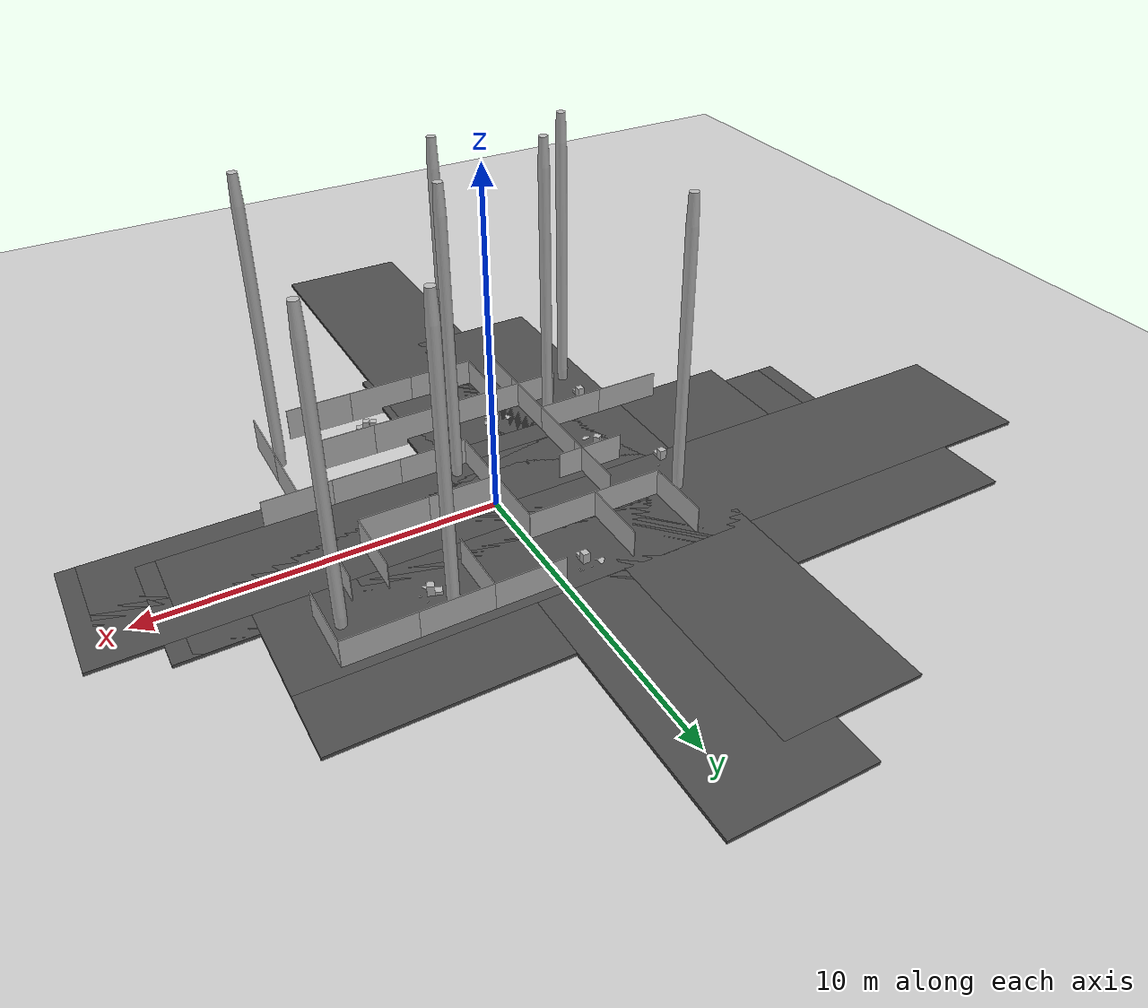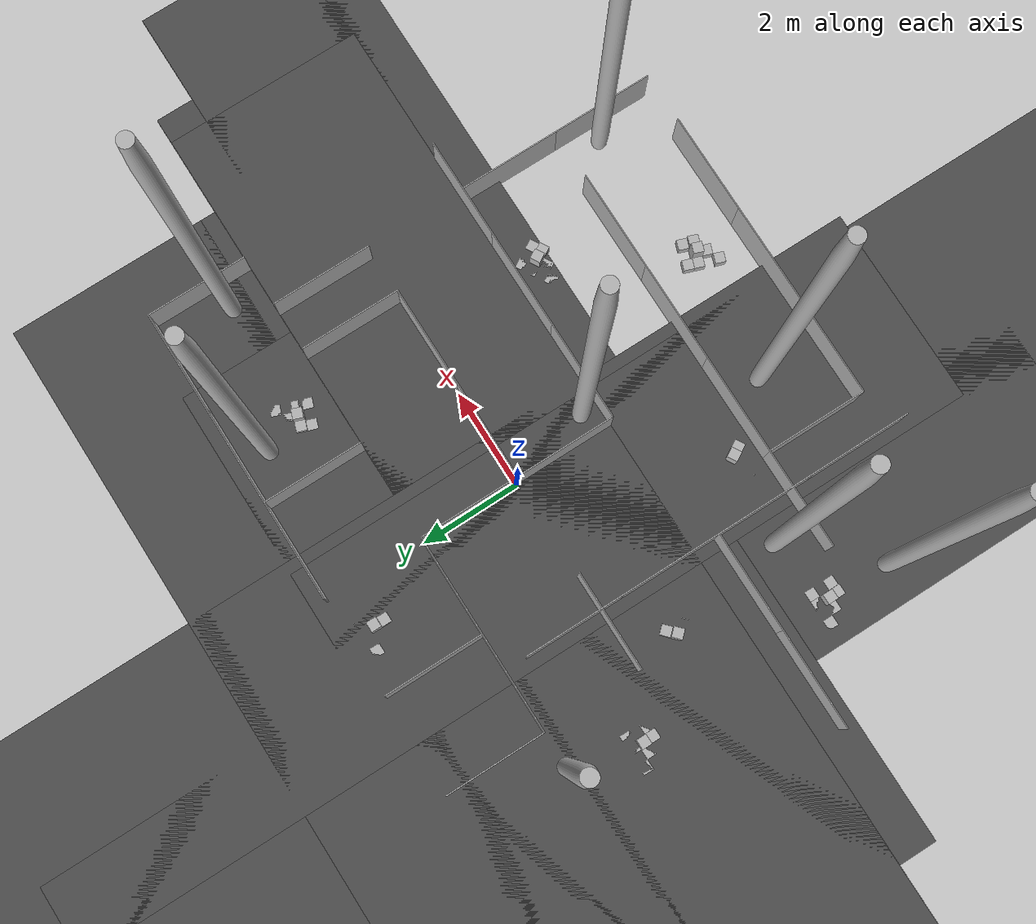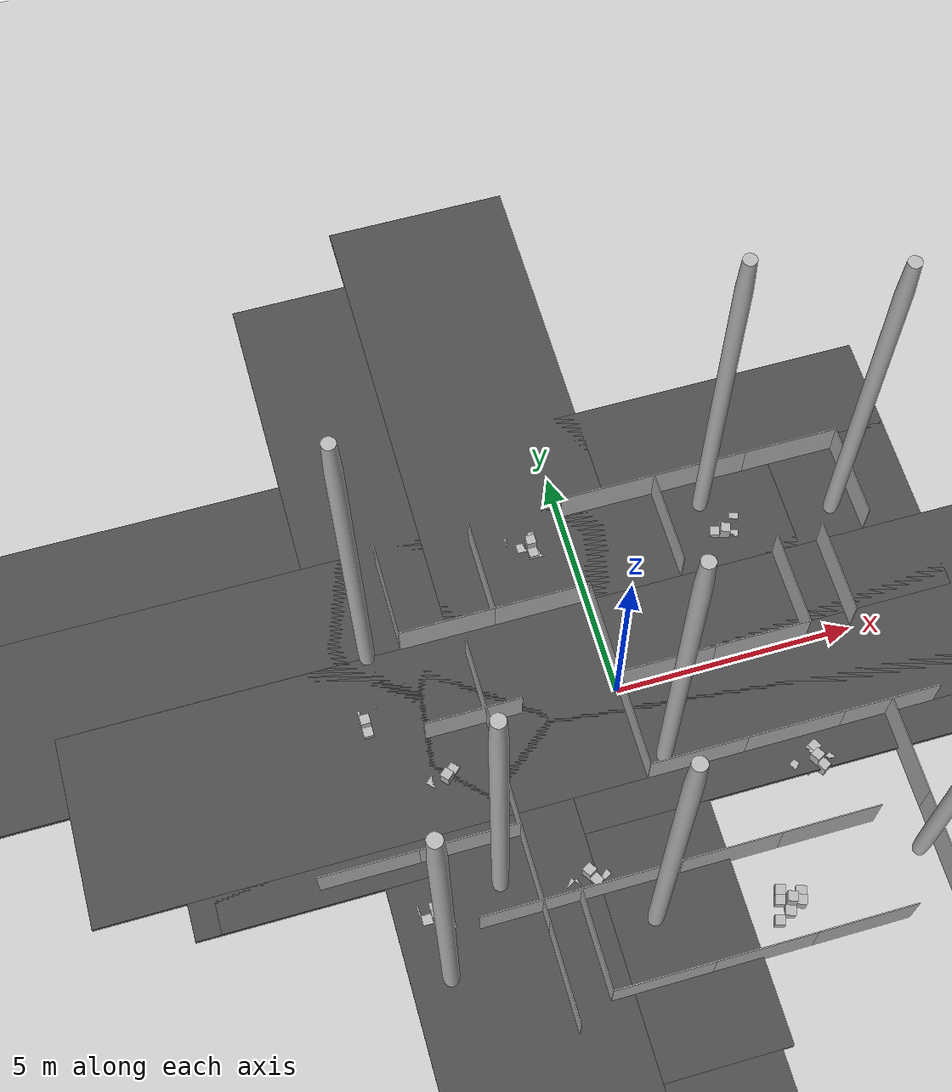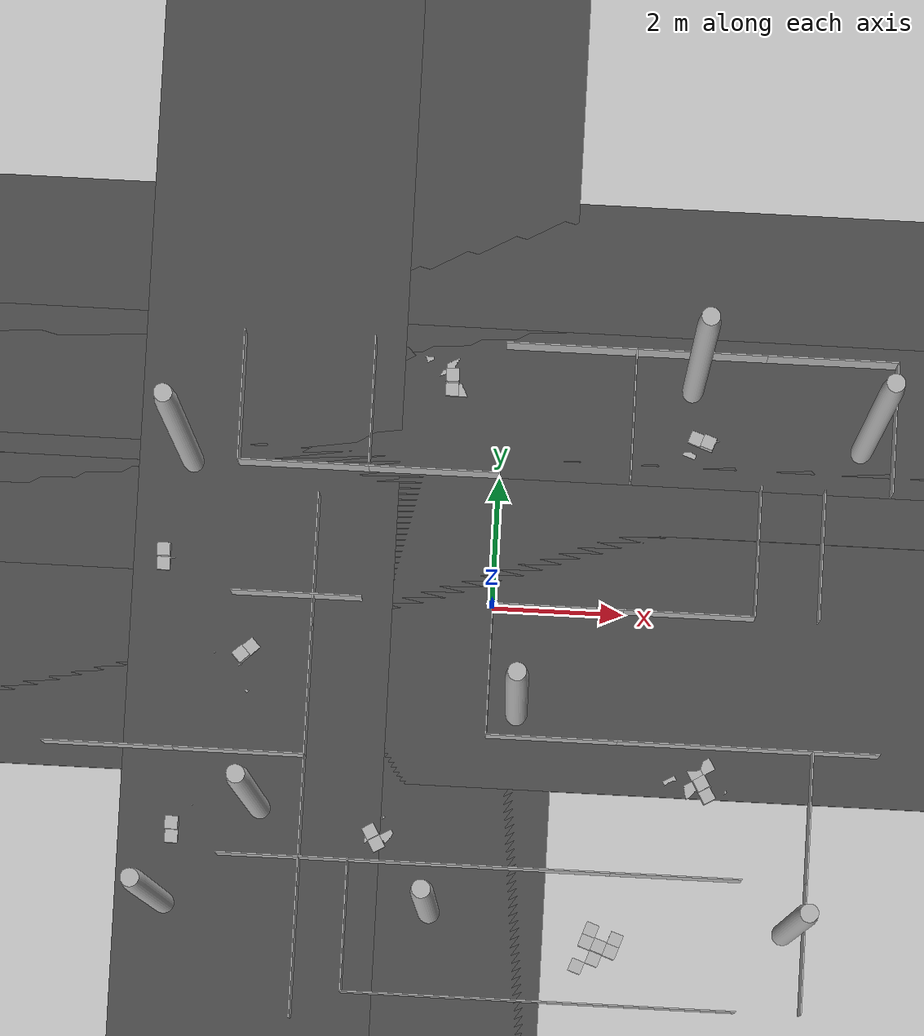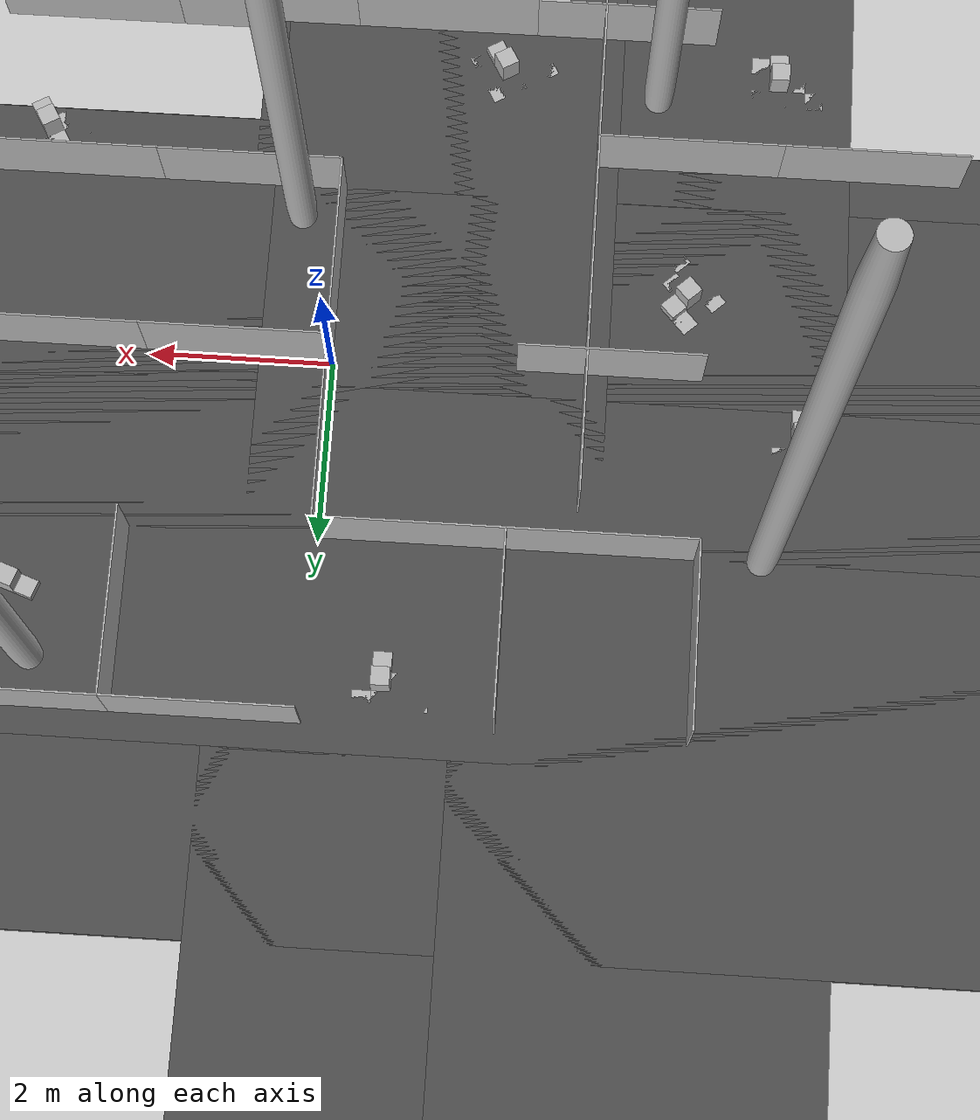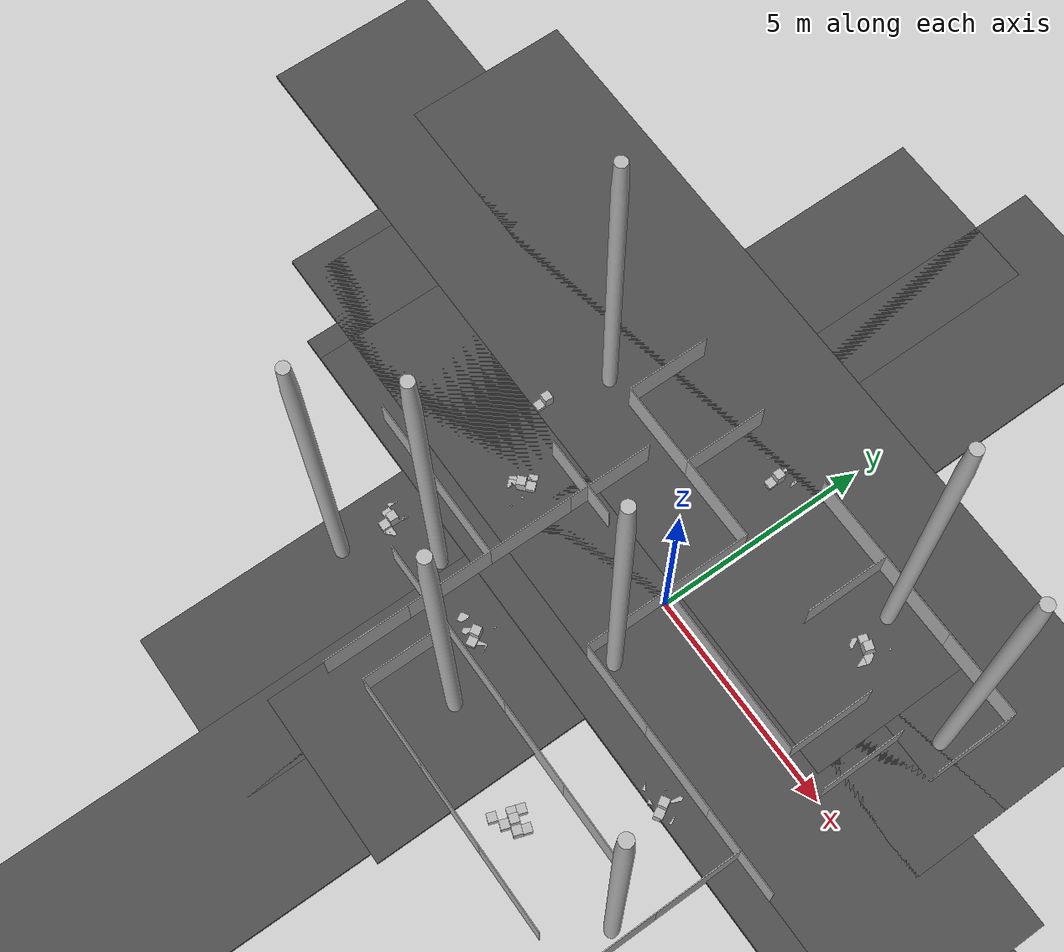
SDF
<?xml version="1.0" ?>
<sdf version="1.4">
  <!--Generated by blend2world.py-->
  <world name="arena_HKT_4">
    <scene>
      <ambient>0.5 0.5 0.5 1</ambient>
      <background>0.5 0.5 0.5 1</background>
      <shadows>false</shadows>
    </scene>
    <plugin name="ros_interface_plugin" filename="librotors_gazebo_ros_interface_plugin.so"></plugin>
    <physics type="ode">
      <gravity>0 0 -9.81</gravity>
      <ode>
        <solver>
          <type>quick</type>
          <iters>1000</iters>
          <sor>1.3</sor>
        </solver>
        <constraints>
          <cfm>0.0</cfm>
          <erp>0.2</erp>
          <contact_max_correcting_vel>100.0</contact_max_correcting_vel>
          <contact_surface_layer>0.001</contact_surface_layer>
        </constraints>
      </ode>
      <real_time_update_rate>100</real_time_update_rate>
      <real_time_factor>1</real_time_factor>
      <max_step_size>0.01</max_step_size>
    </physics>
    <light name="directional_light_1" type="directional">
      <cast_shadows>false</cast_shadows>
      <pose>0 0 30 0.1 0.1 0</pose>
      <diffuse>1.0 1.0 1.0 1</diffuse>
      <specular>.1 .1 .1 1</specular>
      <attenuation>
        <range>300</range>
      </attenuation>
      <direction>0.1 0.1 -1</direction>
    </light>
    <include>
      <uri>model://ground_plane</uri>
    </include>
    <light name="directional_light.-10.0_-12.0" type="sun">
      <pose>-10.0 -12.0 8  0 0 0</pose>
      <cast_shadows>1</cast_shadows>
      <diffuse>0.5 0.5 0.5 1</diffuse>
      <specular>0.1 0.1 0.1 1</specular>
      <attenuation>
        <range>20</range>
        <constant>0.5</constant>
        <linear>0.01</linear>
        <quadratic>0.00</quadratic>
      </attenuation>
      <direction>0.1 0.1 -1.0</direction>
    </light>
    <light name="directional_light.-10.0_0.0" type="sun">
      <pose>-10.0 0.0 8  0 0 0</pose>
      <cast_shadows>1</cast_shadows>
      <diffuse>0.5 0.5 0.5 1</diffuse>
      <specular>0.1 0.1 0.1 1</specular>
      <attenuation>
        <range>20</range>
        <constant>0.5</constant>
        <linear>0.01</linear>
        <quadratic>0.00</quadratic>
      </attenuation>
      <direction>0.1 0.1 -1.0</direction>
    </light>
    <light name="directional_light.-10.0_12.0" type="sun">
      <pose>-10.0 12.0 8  0 0 0</pose>
      <cast_shadows>1</cast_shadows>
      <diffuse>0.5 0.5 0.5 1</diffuse>
      <specular>0.1 0.1 0.1 1</specular>
      <attenuation>
        <range>20</range>
        <constant>0.5</constant>
        <linear>0.01</linear>
        <quadratic>0.00</quadratic>
      </attenuation>
      <direction>0.1 0.1 -1.0</direction>
    </light>
    <light name="directional_light.0.0_-12.0" type="sun">
      <pose>0.0 -12.0 8  0 0 0</pose>
      <cast_shadows>1</cast_shadows>
      <diffuse>0.5 0.5 0.5 1</diffuse>
      <specular>0.1 0.1 0.1 1</specular>
      <attenuation>
        <range>20</range>
        <constant>0.5</constant>
        <linear>0.01</linear>
        <quadratic>0.00</quadratic>
      </attenuation>
      <direction>0.1 0.1 -1.0</direction>
    </light>
    <light name="directional_light.0.0_0.0" type="sun">
      <pose>0.0 0.0 8  0 0 0</pose>
      <cast_shadows>1</cast_shadows>
      <diffuse>0.5 0.5 0.5 1</diffuse>
      <specular>0.1 0.1 0.1 1</specular>
      <attenuation>
        <range>20</range>
        <constant>0.5</constant>
        <linear>0.01</linear>
        <quadratic>0.00</quadratic>
      </attenuation>
      <direction>0.1 0.1 -1.0</direction>
    </light>
    <light name="directional_light.0.0_12.0" type="sun">
      <pose>0.0 12.0 8  0 0 0</pose>
      <cast_shadows>1</cast_shadows>
      <diffuse>0.5 0.5 0.5 1</diffuse>
      <specular>0.1 0.1 0.1 1</specular>
      <attenuation>
        <range>20</range>
        <constant>0.5</constant>
        <linear>0.01</linear>
        <quadratic>0.00</quadratic>
      </attenuation>
      <direction>0.1 0.1 -1.0</direction>
    </light>
    <light name="directional_light.10.0_-12.0" type="sun">
      <pose>10.0 -12.0 8  0 0 0</pose>
      <cast_shadows>1</cast_shadows>
      <diffuse>0.5 0.5 0.5 1</diffuse>
      <specular>0.1 0.1 0.1 1</specular>
      <attenuation>
        <range>20</range>
        <constant>0.5</constant>
        <linear>0.01</linear>
        <quadratic>0.00</quadratic>
      </attenuation>
      <direction>0.1 0.1 -1.0</direction>
    </light>
    <light name="directional_light.10.0_0.0" type="sun">
      <pose>10.0 0.0 8  0 0 0</pose>
      <cast_shadows>1</cast_shadows>
      <diffuse>0.5 0.5 0.5 1</diffuse>
      <specular>0.1 0.1 0.1 1</specular>
      <attenuation>
        <range>20</range>
        <constant>0.5</constant>
        <linear>0.01</linear>
        <quadratic>0.00</quadratic>
      </attenuation>
      <direction>0.1 0.1 -1.0</direction>
    </light>
    <light name="directional_light.10.0_12.0" type="sun">
      <pose>10.0 12.0 8  0 0 0</pose>
      <cast_shadows>1</cast_shadows>
      <diffuse>0.5 0.5 0.5 1</diffuse>
      <specular>0.1 0.1 0.1 1</specular>
      <attenuation>
        <range>20</range>
        <constant>0.5</constant>
        <linear>0.01</linear>
        <quadratic>0.00</quadratic>
      </attenuation>
      <direction>0.1 0.1 -1.0</direction>
    </light>
    <include>
      <name>wall_stand.585</name>
      <pose>2.0 4.19950008392334 0.03449999913573265  0.0 0.0 0.0</pose>
      <uri>model://wall_stand</uri>
    </include>
    <include>
      <name>wall_2x1.265</name>
      <pose>-3.743605136871338 -2.4376254081726074 0.5130000114440918  0.0 -0.0 -3.1430511474609375</pose>
      <uri>model://wall_2x1</uri>
    </include>
    <include>
      <name>wall_stand.586</name>
      <pose>-1.8005000352859497 2.0 0.03449999913573265  0.0 -0.0 1.570796251296997</pose>
      <uri>model://wall_stand</uri>
    </include>
    <include>
      <name>wall_stand.587</name>
      <pose>-0.19949999451637268 2.0 0.03449999913573265  0.0 -0.0 1.570796251296997</pose>
      <uri>model://wall_stand</uri>
    </include>
    <include>
      <name>wall_stand.588</name>
      <pose>-2.740980625152588 -0.6385855674743652 0.03450000286102295  0.0 -0.0 -3.1430511474609375</pose>
      <uri>model://wall_stand</uri>
    </include>
    <include>
      <name>wall_stand.589</name>
      <pose>-2.7433152198791504 -2.239583969116211 0.03450000286102295  0.0 -0.0 -3.1430511474609375</pose>
      <uri>model://wall_stand</uri>
    </include>
    <include>
      <name>wall_2x1.266</name>
      <pose>-2.742147922515869 -1.439084529876709 0.5130000114440918  0.0 -0.0 -1.5722546577453613</pose>
      <uri>model://wall_2x1</uri>
    </include>
    <include>
      <name>wall_2x1.267</name>
      <pose>-2.7392311096191406 0.5609135627746582 0.5130000114440918  0.0 -0.0 -1.5722546577453613</pose>
      <uri>model://wall_2x1</uri>
    </include>
    <include>
      <name>wall_stand.590</name>
      <pose>-2.740398406982422 -0.23958539962768555 0.03450000286102295  0.0 -0.0 -3.1430511474609375</pose>
      <uri>model://wall_stand</uri>
    </include>
    <include>
      <name>wall_stand.591</name>
      <pose>-2.7380638122558594 1.361412525177002 0.03450000286102295  0.0 -0.0 -3.1430511474609375</pose>
      <uri>model://wall_stand</uri>
    </include>
    <include>
      <name>wall_stand.592</name>
      <pose>-2.743896961212158 -2.6385834217071533 0.03450000286102295  0.0 -0.0 -3.1430511474609375</pose>
      <uri>model://wall_stand</uri>
    </include>
    <include>
      <name>wall_stand.593</name>
      <pose>-2.7462315559387207 -4.23958158493042 0.03450000286102295  0.0 -0.0 -3.1430511474609375</pose>
      <uri>model://wall_stand</uri>
    </include>
    <include>
      <name>wall_2x1.268</name>
      <pose>-2.7450642585754395 -3.439082384109497 0.5130000114440918  0.0 -0.0 -1.5722546577453613</pose>
      <uri>model://wall_2x1</uri>
    </include>
    <include>
      <name>wall_2x1.269</name>
      <pose>5.0 4.0 0.5130000114440918  0.0 0.0 0.0</pose>
      <uri>model://wall_2x1</uri>
    </include>
    <include>
      <name>wall_stand.594</name>
      <pose>-0.19949999451637268 2.0 0.03449999913573265  0.0 -0.0 1.570796251296997</pose>
      <uri>model://wall_stand</uri>
    </include>
    <include>
      <name>wall_stand.595</name>
      <pose>-1.8005000352859497 2.0 0.03449999913573265  0.0 -0.0 1.570796251296997</pose>
      <uri>model://wall_stand</uri>
    </include>
    <include>
      <name>wall_2x1.270</name>
      <pose>3.0 4.0 0.5130000114440918  0.0 0.0 0.0</pose>
      <uri>model://wall_2x1</uri>
    </include>
    <include>
      <name>wall_stand.596</name>
      <pose>-1.8005000352859497 2.0 0.03449999913573265  0.0 -0.0 1.570796251296997</pose>
      <uri>model://wall_stand</uri>
    </include>
    <include>
      <name>wall_stand.597</name>
      <pose>-0.19949999451637268 2.0 0.03449999913573265  0.0 -0.0 1.570796251296997</pose>
      <uri>model://wall_stand</uri>
    </include>
    <include>
      <name>wall_2x1.271</name>
      <pose>1.0 4.0 0.5130000114440918  0.0 0.0 0.0</pose>
      <uri>model://wall_2x1</uri>
    </include>
    <include>
      <name>wall_stand.598</name>
      <pose>-1.8005000352859497 2.0 0.03449999913573265  0.0 -0.0 1.570796251296997</pose>
      <uri>model://wall_stand</uri>
    </include>
    <include>
      <name>wall_2x1.272</name>
      <pose>1.0 -2.0 0.5130000114440918  0.0 0.0 0.0</pose>
      <uri>model://wall_2x1</uri>
    </include>
    <include>
      <name>wall_stand.599</name>
      <pose>-1.8005000352859497 2.0 0.03449999913573265  0.0 -0.0 1.570796251296997</pose>
      <uri>model://wall_stand</uri>
    </include>
    <include>
      <name>wall_stand.600</name>
      <pose>-0.19949999451637268 2.0 0.03449999913573265  0.0 -0.0 1.570796251296997</pose>
      <uri>model://wall_stand</uri>
    </include>
    <include>
      <name>wall_2x1.273</name>
      <pose>3.0 -2.0 0.5130000114440918  0.0 0.0 0.0</pose>
      <uri>model://wall_2x1</uri>
    </include>
    <include>
      <name>wall_stand.601</name>
      <pose>-0.19949999451637268 2.0 0.03449999913573265  0.0 -0.0 1.570796251296997</pose>
      <uri>model://wall_stand</uri>
    </include>
    <include>
      <name>wall_stand.602</name>
      <pose>-1.8005000352859497 2.0 0.03449999913573265  0.0 -0.0 1.570796251296997</pose>
      <uri>model://wall_stand</uri>
    </include>
    <include>
      <name>wall_2x1.274</name>
      <pose>5.0 -2.0 0.5130000114440918  0.0 0.0 0.0</pose>
      <uri>model://wall_2x1</uri>
    </include>
    <include>
      <name>wall_stand.603</name>
      <pose>-1.8005000352859497 2.0 0.03449999913573265  0.0 -0.0 1.570796251296997</pose>
      <uri>model://wall_stand</uri>
    </include>
    <include>
      <name>wall_stand.604</name>
      <pose>-0.19949999451637268 2.0 0.03449999913573265  0.0 -0.0 1.570796251296997</pose>
      <uri>model://wall_stand</uri>
    </include>
    <include>
      <name>wall_2x1.275</name>
      <pose>4.982755661010742 -3.0 0.5130000114440918  0.0 -0.0 1.570796251296997</pose>
      <uri>model://wall_2x1</uri>
    </include>
    <include>
      <name>wall_stand.605</name>
      <pose>0.0 1.8005001544952393 0.03449999913573265  0.0 0.0 0.0</pose>
      <uri>model://wall_stand</uri>
    </include>
    <include>
      <name>wall_stand.606</name>
      <pose>0.0 0.19949999451637268 0.03449999913573265  0.0 0.0 0.0</pose>
      <uri>model://wall_stand</uri>
    </include>
    <include>
      <name>wall_2x1.276</name>
      <pose>4.982755661010742 -5.0 0.5130000114440918  0.0 -0.0 1.570796251296997</pose>
      <uri>model://wall_2x1</uri>
    </include>
    <include>
      <name>wall_stand.607</name>
      <pose>0.0 0.19949999451637268 0.03449999913573265  0.0 0.0 0.0</pose>
      <uri>model://wall_stand</uri>
    </include>
    <include>
      <name>wall_stand.608</name>
      <pose>0.0 1.8005001544952393 0.03449999913573265  0.0 0.0 0.0</pose>
      <uri>model://wall_stand</uri>
    </include>
    <include>
      <name>wall_2x1.277</name>
      <pose>-2.0 -5.0 0.5130000114440918  0.0 -0.0 1.570796251296997</pose>
      <uri>model://wall_2x1</uri>
    </include>
    <include>
      <name>wall_stand.609</name>
      <pose>0.0 0.19949999451637268 0.03449999913573265  0.0 0.0 0.0</pose>
      <uri>model://wall_stand</uri>
    </include>
    <include>
      <name>wall_stand.610</name>
      <pose>0.0 1.8005001544952393 0.03449999913573265  0.0 0.0 0.0</pose>
      <uri>model://wall_stand</uri>
    </include>
    <include>
      <name>wall_2x1.278</name>
      <pose>-1.0 -6.0 0.5130000114440918  0.0 0.0 0.0</pose>
      <uri>model://wall_2x1</uri>
    </include>
    <include>
      <name>wall_stand.611</name>
      <pose>-1.8005000352859497 2.0 0.03449999913573265  0.0 -0.0 1.570796251296997</pose>
      <uri>model://wall_stand</uri>
    </include>
    <include>
      <name>wall_stand.612</name>
      <pose>-0.19949999451637268 2.0 0.03449999913573265  0.0 -0.0 1.570796251296997</pose>
      <uri>model://wall_stand</uri>
    </include>
    <include>
      <name>wall_2x1.279</name>
      <pose>1.0 -6.0 0.5130000114440918  0.0 0.0 0.0</pose>
      <uri>model://wall_2x1</uri>
    </include>
    <include>
      <name>wall_stand.613</name>
      <pose>-0.19949999451637268 2.0 0.03449999913573265  0.0 -0.0 1.570796251296997</pose>
      <uri>model://wall_stand</uri>
    </include>
    <include>
      <name>wall_stand.614</name>
      <pose>-1.8005000352859497 2.0 0.03449999913573265  0.0 -0.0 1.570796251296997</pose>
      <uri>model://wall_stand</uri>
    </include>
    <include>
      <name>wall_2x1.280</name>
      <pose>3.0 -6.0 0.5130000114440918  0.0 0.0 0.0</pose>
      <uri>model://wall_2x1</uri>
    </include>
    <include>
      <name>wall_stand.615</name>
      <pose>-1.8005000352859497 2.0 0.03449999913573265  0.0 -0.0 1.570796251296997</pose>
      <uri>model://wall_stand</uri>
    </include>
    <include>
      <name>wall_stand.616</name>
      <pose>-0.19949999451637268 2.0 0.03449999913573265  0.0 -0.0 1.570796251296997</pose>
      <uri>model://wall_stand</uri>
    </include>
    <include>
      <name>wall_2x1.281</name>
      <pose>4.976974010467529 1.0 0.5130000114440918  0.0 -0.0 1.570796251296997</pose>
      <uri>model://wall_2x1</uri>
    </include>
    <include>
      <name>wall_stand.617</name>
      <pose>0.0 1.8005001544952393 0.03449999913573265  0.0 0.0 0.0</pose>
      <uri>model://wall_stand</uri>
    </include>
    <include>
      <name>wall_stand.618</name>
      <pose>0.0 0.19949999451637268 0.03449999913573265  0.0 0.0 0.0</pose>
      <uri>model://wall_stand</uri>
    </include>
    <include>
      <name>wall_2x1.282</name>
      <pose>6.0 3.0 0.5130000114440918  0.0 -0.0 1.570796251296997</pose>
      <uri>model://wall_2x1</uri>
    </include>
    <include>
      <name>wall_stand.619</name>
      <pose>0.0 0.19949999451637268 0.03449999913573265  0.0 0.0 0.0</pose>
      <uri>model://wall_stand</uri>
    </include>
    <include>
      <name>wall_stand.620</name>
      <pose>0.0 1.8005001544952393 0.03449999913573265  0.0 0.0 0.0</pose>
      <uri>model://wall_stand</uri>
    </include>
    <include>
      <name>wall_stand.621</name>
      <pose>0.0 0.19949999451637268 0.03449999913573265  0.0 0.0 0.0</pose>
      <uri>model://wall_stand</uri>
    </include>
    <include>
      <name>wall_stand.622</name>
      <pose>-1.8005000352859497 2.0 0.03449999913573265  0.0 -0.0 1.570796251296997</pose>
      <uri>model://wall_stand</uri>
    </include>
    <include>
      <name>wall_stand.623</name>
      <pose>-0.19949999451637268 2.0 0.03449999913573265  0.0 -0.0 1.570796251296997</pose>
      <uri>model://wall_stand</uri>
    </include>
    <include>
      <name>wall_stand.624</name>
      <pose>-0.19949999451637268 2.0 0.03449999913573265  0.0 -0.0 1.570796251296997</pose>
      <uri>model://wall_stand</uri>
    </include>
    <include>
      <name>wall_stand.625</name>
      <pose>0.0 1.8005001544952393 0.03449999913573265  0.0 0.0 0.0</pose>
      <uri>model://wall_stand</uri>
    </include>
    <include>
      <name>wall_stand.626</name>
      <pose>0.0 0.19949999451637268 0.03449999913573265  0.0 0.0 0.0</pose>
      <uri>model://wall_stand</uri>
    </include>
    <include>
      <name>wall_stand.627</name>
      <pose>-1.8005000352859497 2.0 0.03449999913573265  0.0 -0.0 1.570796251296997</pose>
      <uri>model://wall_stand</uri>
    </include>
    <include>
      <name>wall_2x1.283</name>
      <pose>0.0 -1.0 0.5130000114440918  0.0 -0.0 1.570796251296997</pose>
      <uri>model://wall_2x1</uri>
    </include>
    <include>
      <name>wall_stand.628</name>
      <pose>0.0 0.19949999451637268 0.03449999913573265  0.0 0.0 0.0</pose>
      <uri>model://wall_stand</uri>
    </include>
    <include>
      <name>wall_stand.629</name>
      <pose>0.0 1.8005001544952393 0.03449999913573265  0.0 0.0 0.0</pose>
      <uri>model://wall_stand</uri>
    </include>
    <include>
      <name>wall_2x1.284</name>
      <pose>3.0 -4.0 0.5130000114440918  0.0 0.0 0.0</pose>
      <uri>model://wall_2x1</uri>
    </include>
    <include>
      <name>wall_stand.630</name>
      <pose>-0.19949999451637268 2.0 0.03449999913573265  0.0 -0.0 1.570796251296997</pose>
      <uri>model://wall_stand</uri>
    </include>
    <include>
      <name>wall_stand.631</name>
      <pose>-1.8005000352859497 2.0 0.03449999913573265  0.0 -0.0 1.570796251296997</pose>
      <uri>model://wall_stand</uri>
    </include>
    <include>
      <name>wall_2x1.285</name>
      <pose>1.0 -4.0 0.5130000114440918  0.0 0.0 0.0</pose>
      <uri>model://wall_2x1</uri>
    </include>
    <include>
      <name>wall_stand.632</name>
      <pose>-1.8005000352859497 2.0 0.03449999913573265  0.0 -0.0 1.570796251296997</pose>
      <uri>model://wall_stand</uri>
    </include>
    <include>
      <name>wall_stand.633</name>
      <pose>-0.19949999451637268 2.0 0.03449999913573265  0.0 -0.0 1.570796251296997</pose>
      <uri>model://wall_stand</uri>
    </include>
    <include>
      <name>wall_2x1.286</name>
      <pose>-1.0 -4.0 0.5130000114440918  0.0 0.0 0.0</pose>
      <uri>model://wall_2x1</uri>
    </include>
    <include>
      <name>wall_stand.634</name>
      <pose>-0.19949999451637268 2.0 0.03449999913573265  0.0 -0.0 1.570796251296997</pose>
      <uri>model://wall_stand</uri>
    </include>
    <include>
      <name>wall_stand.635</name>
      <pose>-1.8005000352859497 2.0 0.03449999913573265  0.0 -0.0 1.570796251296997</pose>
      <uri>model://wall_stand</uri>
    </include>
    <include>
      <name>wall_2x1.287</name>
      <pose>-3.0 -4.0 0.5130000114440918  0.0 0.0 0.0</pose>
      <uri>model://wall_2x1</uri>
    </include>
    <include>
      <name>wall_stand.636</name>
      <pose>-1.8005000352859497 2.0 0.03449999913573265  0.0 -0.0 1.570796251296997</pose>
      <uri>model://wall_stand</uri>
    </include>
    <include>
      <name>wall_stand.637</name>
      <pose>-0.19949999451637268 2.0 0.03449999913573265  0.0 -0.0 1.570796251296997</pose>
      <uri>model://wall_stand</uri>
    </include>
    <include>
      <name>wall_2x1.288</name>
      <pose>-5.743602752685547 -2.434708595275879 0.5130000114440918  0.0 -0.0 -3.1430511474609375</pose>
      <uri>model://wall_2x1</uri>
    </include>
    <include>
      <name>wall_stand.638</name>
      <pose>-0.19949999451637268 2.0 0.03449999913573265  0.0 -0.0 1.570796251296997</pose>
      <uri>model://wall_stand</uri>
    </include>
    <include>
      <name>wall_stand.639</name>
      <pose>-1.8005000352859497 2.0 0.03449999913573265  0.0 -0.0 1.570796251296997</pose>
      <uri>model://wall_stand</uri>
    </include>
    <include>
      <name>wall_2x1.289</name>
      <pose>3.0 0.0 0.5130000114440918  0.0 0.0 0.0</pose>
      <uri>model://wall_2x1</uri>
    </include>
    <include>
      <name>wall_stand.640</name>
      <pose>0.19949999451637268 0.0 0.03449999913573265  0.0 -0.0 1.570796251296997</pose>
      <uri>model://wall_stand</uri>
    </include>
    <include>
      <name>wall_stand.641</name>
      <pose>1.8005000352859497 0.0 0.03449999913573265  0.0 -0.0 1.570796251296997</pose>
      <uri>model://wall_stand</uri>
    </include>
    <include>
      <name>wall_2x1.290</name>
      <pose>4.0 1.0 0.5130000114440918  0.0 -0.0 1.570796251296997</pose>
      <uri>model://wall_2x1</uri>
    </include>
    <include>
      <name>wall_stand.642</name>
      <pose>0.0 0.19949999451637268 0.03449999913573265  0.0 0.0 0.0</pose>
      <uri>model://wall_stand</uri>
    </include>
    <include>
      <name>wall_stand.643</name>
      <pose>0.0 1.8005001544952393 0.03449999913573265  0.0 0.0 0.0</pose>
      <uri>model://wall_stand</uri>
    </include>
    <include>
      <name>wall_2x1.291</name>
      <pose>-3.0 0.0 0.5130000114440918  0.0 0.0 0.0</pose>
      <uri>model://wall_2x1</uri>
    </include>
    <include>
      <name>wall_stand.644</name>
      <pose>-1.8005000352859497 2.0 0.03449999913573265  0.0 -0.0 1.570796251296997</pose>
      <uri>model://wall_stand</uri>
    </include>
    <include>
      <name>wall_stand.645</name>
      <pose>-0.19949999451637268 2.0 0.03449999913573265  0.0 -0.0 1.570796251296997</pose>
      <uri>model://wall_stand</uri>
    </include>
    <include>
      <name>wall_2x1.292</name>
      <pose>-3.0 2.0 0.5130000114440918  0.0 0.0 0.0</pose>
      <uri>model://wall_2x1</uri>
    </include>
    <include>
      <name>wall_stand.646</name>
      <pose>-0.19949999451637268 2.0 0.03449999913573265  0.0 -0.0 1.570796251296997</pose>
      <uri>model://wall_stand</uri>
    </include>
    <include>
      <name>wall_stand.647</name>
      <pose>-1.8005000352859497 2.0 0.03449999913573265  0.0 -0.0 1.570796251296997</pose>
      <uri>model://wall_stand</uri>
    </include>
    <include>
      <name>cube_20x20.681</name>
      <pose>-0.800000011920929 3.718953847885132 0.10000000149011612  0.0 -0.0 3.141592502593994</pose>
      <uri>model://cube_20x20</uri>
    </include>
    <include>
      <name>cube_20x20.682</name>
      <pose>-1.0 3.518953800201416 0.10000000149011612  0.0 -0.0 3.141592502593994</pose>
      <uri>model://cube_20x20</uri>
    </include>
    <include>
      <name>cube_20x20.683</name>
      <pose>-1.2000000476837158 3.718953847885132 0.10000000149011612  0.0 -0.0 3.141592502593994</pose>
      <uri>model://cube_20x20</uri>
    </include>
    <include>
      <name>cube_20x20.684</name>
      <pose>-0.6000000238418579 3.718953847885132 0.10000000149011612  0.0 -0.0 3.141592502593994</pose>
      <uri>model://cube_20x20</uri>
    </include>
    <include>
      <name>cube_20x20.685</name>
      <pose>-0.6000000238418579 3.3189537525177 0.10000000149011612  0.0 -0.0 3.141592502593994</pose>
      <uri>model://cube_20x20</uri>
    </include>
    <include>
      <name>cube_20x30.028</name>
      <pose>-0.800000011920929 3.3189537525177 0.15000000596046448  0.0 -0.0 3.141592502593994</pose>
      <uri>model://cube_20x30</uri>
    </include>
    <include>
      <name>cube_20x50.028</name>
      <pose>-0.800000011920929 3.518953800201416 0.25  0.0 -0.0 3.141592502593994</pose>
      <uri>model://cube_20x50</uri>
    </include>
    <include>
      <name>ramp.051</name>
      <pose>-1.2133511304855347 -5.680870532989502 0.15000000596046448  0.0 -0.0 4.71238899230957</pose>
      <uri>model://ramp</uri>
    </include>
    <include>
      <name>ramp.052</name>
      <pose>-0.9832800030708313 2.2666399478912354 0.15000000596046448  0.0 -0.0 7.853981971740723</pose>
      <uri>model://ramp</uri>
    </include>
    <include>
      <name>wall_2x1.293</name>
      <pose>1.0 0.0 0.5130000114440918  0.0 0.0 0.0</pose>
      <uri>model://wall_2x1</uri>
    </include>
    <include>
      <name>wall_stand.648</name>
      <pose>1.8005000352859497 0.0 0.03449999913573265  0.0 -0.0 1.570796251296997</pose>
      <uri>model://wall_stand</uri>
    </include>
    <include>
      <name>wall_stand.649</name>
      <pose>0.19949999451637268 0.0 0.03449999913573265  0.0 -0.0 1.570796251296997</pose>
      <uri>model://wall_stand</uri>
    </include>
    <include>
      <name>wall_2x1.294</name>
      <pose>0.0 1.0 0.5130000114440918  0.0 -0.0 1.570796251296997</pose>
      <uri>model://wall_2x1</uri>
    </include>
    <include>
      <name>wall_stand.650</name>
      <pose>0.0 1.8005001544952393 0.03449999913573265  0.0 0.0 0.0</pose>
      <uri>model://wall_stand</uri>
    </include>
    <include>
      <name>wall_stand.651</name>
      <pose>0.0 0.19949999451637268 0.03449999913573265  0.0 0.0 0.0</pose>
      <uri>model://wall_stand</uri>
    </include>
    <include>
      <name>wall_2x1.295</name>
      <pose>-4.0 3.0 0.5130000114440918  0.0 -0.0 1.570796251296997</pose>
      <uri>model://wall_2x1</uri>
    </include>
    <include>
      <name>wall_2x1.296</name>
      <pose>-2.0 3.0 0.5130000114440918  0.0 -0.0 1.570796251296997</pose>
      <uri>model://wall_2x1</uri>
    </include>
    <include>
      <name>wall_2x1.297</name>
      <pose>-2.7479805946350098 -5.439080238342285 0.5130000114440918  0.0 -0.0 -1.5722546577453613</pose>
      <uri>model://wall_2x1</uri>
    </include>
    <include>
      <name>wall_2x1.298</name>
      <pose>2.0 3.0 0.5130000114440918  0.0 -0.0 1.570796251296997</pose>
      <uri>model://wall_2x1</uri>
    </include>
    <include>
      <name>wall_2x1.299</name>
      <pose>-1.0 2.0 0.5130000114440918  0.0 0.0 0.0</pose>
      <uri>model://wall_2x1</uri>
    </include>
    <include>
      <name>wall_stand.652</name>
      <pose>-1.8005000352859497 2.0 0.03449999913573265  0.0 -0.0 1.570796251296997</pose>
      <uri>model://wall_stand</uri>
    </include>
    <include>
      <name>wall_stand.653</name>
      <pose>-0.19949999451637268 2.0 0.03449999913573265  0.0 -0.0 1.570796251296997</pose>
      <uri>model://wall_stand</uri>
    </include>
    <include>
      <name>wall_stand.654</name>
      <pose>-4.0 2.19950008392334 0.03449999913573265  0.0 0.0 0.0</pose>
      <uri>model://wall_stand</uri>
    </include>
    <include>
      <name>wall_stand.655</name>
      <pose>2.0 2.19950008392334 0.03449999913573265  0.0 0.0 0.0</pose>
      <uri>model://wall_stand</uri>
    </include>
    <include>
      <name>wall_stand.656</name>
      <pose>-2.0 2.19950008392334 0.03449999913573265  0.0 0.0 0.0</pose>
      <uri>model://wall_stand</uri>
    </include>
    <include>
      <name>wall_stand.657</name>
      <pose>2.0 3.817974328994751 0.03449999913573265  0.0 0.0 0.0</pose>
      <uri>model://wall_stand</uri>
    </include>
    <include>
      <name>wall_stand.658</name>
      <pose>-2.0 3.8005001544952393 0.03449999913573265  0.0 0.0 0.0</pose>
      <uri>model://wall_stand</uri>
    </include>
    <include>
      <name>wall_stand.659</name>
      <pose>-2.749147891998291 -6.239579677581787 0.03450000286102295  0.0 -0.0 -3.1430511474609375</pose>
      <uri>model://wall_stand</uri>
    </include>
    <include>
      <name>wall_stand.660</name>
      <pose>-2.7468132972717285 -4.638580799102783 0.03450000286102295  0.0 -0.0 -3.1430511474609375</pose>
      <uri>model://wall_stand</uri>
    </include>
    <include>
      <name>wall_stand.661</name>
      <pose>-4.0 3.8005001544952393 0.03449999913573265  0.0 0.0 0.0</pose>
      <uri>model://wall_stand</uri>
    </include>
    <include>
      <name>cube_20x20.686</name>
      <pose>-5.073810577392578 0.8086726665496826 0.10000000149011612  0.0 -0.0 3.141592502593994</pose>
      <uri>model://cube_20x20</uri>
    </include>
    <include>
      <name>cube_20x20.687</name>
      <pose>-5.273810386657715 0.6086728572845459 0.10000000149011612  0.0 -0.0 3.141592502593994</pose>
      <uri>model://cube_20x20</uri>
    </include>
    <include>
      <name>cube_20x20.688</name>
      <pose>-5.473810195922852 0.8086726665496826 0.10000000149011612  0.0 -0.0 3.141592502593994</pose>
      <uri>model://cube_20x20</uri>
    </include>
    <include>
      <name>cube_20x20.689</name>
      <pose>-4.873810291290283 0.8086726665496826 0.10000000149011612  0.0 -0.0 3.141592502593994</pose>
      <uri>model://cube_20x20</uri>
    </include>
    <include>
      <name>cube_20x20.690</name>
      <pose>-4.873810291290283 0.4086730480194092 0.10000000149011612  0.0 -0.0 3.141592502593994</pose>
      <uri>model://cube_20x20</uri>
    </include>
    <include>
      <name>cube_20x20.691</name>
      <pose>-5.073810577392578 0.8086726665496826 0.10000000149011612  0.0 -0.0 3.141592502593994</pose>
      <uri>model://cube_20x20</uri>
    </include>
    <include>
      <name>cube_20x20.692</name>
      <pose>-5.273810386657715 0.6086728572845459 0.10000000149011612  0.0 -0.0 3.141592502593994</pose>
      <uri>model://cube_20x20</uri>
    </include>
    <include>
      <name>cube_20x20.693</name>
      <pose>-5.473810195922852 0.8086726665496826 0.10000000149011612  0.0 -0.0 3.141592502593994</pose>
      <uri>model://cube_20x20</uri>
    </include>
    <include>
      <name>cube_20x20.694</name>
      <pose>-4.873810291290283 0.8086726665496826 0.10000000149011612  0.0 -0.0 3.141592502593994</pose>
      <uri>model://cube_20x20</uri>
    </include>
    <include>
      <name>cube_20x20.695</name>
      <pose>-4.873810291290283 0.4086730480194092 0.10000000149011612  0.0 -0.0 3.141592502593994</pose>
      <uri>model://cube_20x20</uri>
    </include>
    <include>
      <name>cube_20x20.696</name>
      <pose>-4.71690034866333 -3.3630831241607666 0.10000000149011612  0.0 -0.0 3.141592502593994</pose>
      <uri>model://cube_20x20</uri>
    </include>
    <include>
      <name>cube_20x20.697</name>
      <pose>-4.916900157928467 -3.5630829334259033 0.10000000149011612  0.0 -0.0 3.141592502593994</pose>
      <uri>model://cube_20x20</uri>
    </include>
    <include>
      <name>cube_20x20.698</name>
      <pose>-5.1168999671936035 -3.3630831241607666 0.10000000149011612  0.0 -0.0 3.141592502593994</pose>
      <uri>model://cube_20x20</uri>
    </include>
    <include>
      <name>cube_20x20.699</name>
      <pose>-4.516900062561035 -3.3630831241607666 0.10000000149011612  0.0 -0.0 3.141592502593994</pose>
      <uri>model://cube_20x20</uri>
    </include>
    <include>
      <name>cube_20x20.700</name>
      <pose>-4.516900062561035 -3.76308274269104 0.10000000149011612  0.0 -0.0 3.141592502593994</pose>
      <uri>model://cube_20x20</uri>
    </include>
    <include>
      <name>cube_20x20.701</name>
      <pose>-4.71690034866333 -3.3630831241607666 0.10000000149011612  0.0 -0.0 3.141592502593994</pose>
      <uri>model://cube_20x20</uri>
    </include>
    <include>
      <name>cube_20x20.702</name>
      <pose>-4.916900157928467 -3.5630829334259033 0.10000000149011612  0.0 -0.0 3.141592502593994</pose>
      <uri>model://cube_20x20</uri>
    </include>
    <include>
      <name>cube_20x20.703</name>
      <pose>-5.1168999671936035 -3.3630831241607666 0.10000000149011612  0.0 -0.0 3.141592502593994</pose>
      <uri>model://cube_20x20</uri>
    </include>
    <include>
      <name>cube_20x20.704</name>
      <pose>-4.516900062561035 -3.3630831241607666 0.10000000149011612  0.0 -0.0 3.141592502593994</pose>
      <uri>model://cube_20x20</uri>
    </include>
    <include>
      <name>cube_20x20.705</name>
      <pose>-4.516900062561035 -3.76308274269104 0.10000000149011612  0.0 -0.0 3.141592502593994</pose>
      <uri>model://cube_20x20</uri>
    </include>
    <include>
      <name>cube_20x20.706</name>
      <pose>-1.7805752754211426 -3.3717634677886963 0.10000000149011612  0.0 -0.0 3.6651763916015625</pose>
      <uri>model://cube_20x20</uri>
    </include>
    <include>
      <name>cube_20x20.707</name>
      <pose>-1.8537843227386475 -3.6449673175811768 0.10000000149011612  0.0 -0.0 3.6651763916015625</pose>
      <uri>model://cube_20x20</uri>
    </include>
    <include>
      <name>cube_20x20.708</name>
      <pose>-2.126988172531128 -3.5717580318450928 0.10000000149011612  0.0 -0.0 3.6651763916015625</pose>
      <uri>model://cube_20x20</uri>
    </include>
    <include>
      <name>cube_20x20.709</name>
      <pose>-1.6073683500289917 -3.271765947341919 0.10000000149011612  0.0 -0.0 3.6651763916015625</pose>
      <uri>model://cube_20x20</uri>
    </include>
    <include>
      <name>cube_20x20.710</name>
      <pose>-1.4073739051818848 -3.6181790828704834 0.10000000149011612  0.0 -0.0 3.6651763916015625</pose>
      <uri>model://cube_20x20</uri>
    </include>
    <include>
      <name>cube_20x20.711</name>
      <pose>-1.7805752754211426 -3.3717634677886963 0.10000000149011612  0.0 -0.0 3.6651763916015625</pose>
      <uri>model://cube_20x20</uri>
    </include>
    <include>
      <name>cube_20x20.712</name>
      <pose>-1.8537843227386475 -3.6449673175811768 0.10000000149011612  0.0 -0.0 3.6651763916015625</pose>
      <uri>model://cube_20x20</uri>
    </include>
    <include>
      <name>cube_20x20.713</name>
      <pose>-2.126988172531128 -3.5717580318450928 0.10000000149011612  0.0 -0.0 3.6651763916015625</pose>
      <uri>model://cube_20x20</uri>
    </include>
    <include>
      <name>cube_20x20.714</name>
      <pose>-1.6073683500289917 -3.271765947341919 0.10000000149011612  0.0 -0.0 3.6651763916015625</pose>
      <uri>model://cube_20x20</uri>
    </include>
    <include>
      <name>cube_20x20.715</name>
      <pose>-1.4073739051818848 -3.6181790828704834 0.10000000149011612  0.0 -0.0 3.6651763916015625</pose>
      <uri>model://cube_20x20</uri>
    </include>
    <include>
      <name>cube_20x20.716</name>
      <pose>-3.9528942108154297 -1.071094274520874 0.10000000149011612  0.0 0.0 5.4528021812438965</pose>
      <uri>model://cube_20x20</uri>
    </include>
    <include>
      <name>cube_20x20.717</name>
      <pose>-3.6703381538391113 -1.0838134288787842 0.10000000149011612  0.0 0.0 5.4528021812438965</pose>
      <uri>model://cube_20x20</uri>
    </include>
    <include>
      <name>cube_20x20.718</name>
      <pose>-3.6830577850341797 -1.3663697242736816 0.10000000149011612  0.0 0.0 5.4528021812438965</pose>
      <uri>model://cube_20x20</uri>
    </include>
    <include>
      <name>cube_20x20.720</name>
      <pose>-3.792536735534668 -0.6536192893981934 0.10000000149011612  0.0 0.0 5.4528021812438965</pose>
      <uri>model://cube_20x20</uri>
    </include>
    <include>
      <name>cube_20x20.721</name>
      <pose>-3.9528942108154297 -1.071094274520874 0.10000000149011612  0.0 0.0 5.4528021812438965</pose>
      <uri>model://cube_20x20</uri>
    </include>
    <include>
      <name>cube_20x20.722</name>
      <pose>-3.6703381538391113 -1.0838134288787842 0.10000000149011612  0.0 0.0 5.4528021812438965</pose>
      <uri>model://cube_20x20</uri>
    </include>
    <include>
      <name>cube_20x20.723</name>
      <pose>-3.6830577850341797 -1.3663697242736816 0.10000000149011612  0.0 0.0 5.4528021812438965</pose>
      <uri>model://cube_20x20</uri>
    </include>
    <include>
      <name>cube_20x20.724</name>
      <pose>-4.087812423706055 -0.9234559535980225 0.10000000149011612  0.0 0.0 5.4528021812438965</pose>
      <uri>model://cube_20x20</uri>
    </include>
    <include>
      <name>cube_20x20.725</name>
      <pose>-3.792536735534668 -0.6536192893981934 0.10000000149011612  0.0 0.0 5.4528021812438965</pose>
      <uri>model://cube_20x20</uri>
    </include>
    <include>
      <name>cube_20x20.726</name>
      <pose>3.3604865074157715 2.6194584369659424 0.10000000149011612  0.0 0.0 7.517675399780273</pose>
      <uri>model://cube_20x20</uri>
    </include>
    <include>
      <name>cube_20x20.727</name>
      <pose>3.2376906871795654 2.8742544651031494 0.10000000149011612  0.0 0.0 7.517675399780273</pose>
      <uri>model://cube_20x20</uri>
    </include>
    <include>
      <name>cube_20x20.728</name>
      <pose>3.4924871921539307 2.9970500469207764 0.10000000149011612  0.0 0.0 7.517675399780273</pose>
      <uri>model://cube_20x20</uri>
    </include>
    <include>
      <name>cube_20x20.729</name>
      <pose>3.294485569000244 2.4306623935699463 0.10000000149011612  0.0 0.0 7.517675399780273</pose>
      <uri>model://cube_20x20</uri>
    </include>
    <include>
      <name>cube_20x20.730</name>
      <pose>2.91689395904541 2.5626633167266846 0.10000000149011612  0.0 0.0 7.517675399780273</pose>
      <uri>model://cube_20x20</uri>
    </include>
    <include>
      <name>cube_20x20.731</name>
      <pose>3.3604865074157715 2.6194584369659424 0.10000000149011612  0.0 0.0 7.517675399780273</pose>
      <uri>model://cube_20x20</uri>
    </include>
    <include>
      <name>cube_20x20.732</name>
      <pose>3.2376906871795654 2.8742544651031494 0.10000000149011612  0.0 0.0 7.517675399780273</pose>
      <uri>model://cube_20x20</uri>
    </include>
    <include>
      <name>cube_20x20.733</name>
      <pose>3.4924871921539307 2.9970500469207764 0.10000000149011612  0.0 0.0 7.517675399780273</pose>
      <uri>model://cube_20x20</uri>
    </include>
    <include>
      <name>cube_20x20.734</name>
      <pose>3.294485569000244 2.4306623935699463 0.10000000149011612  0.0 0.0 7.517675399780273</pose>
      <uri>model://cube_20x20</uri>
    </include>
    <include>
      <name>cube_20x20.735</name>
      <pose>2.91689395904541 2.5626633167266846 0.10000000149011612  0.0 0.0 7.517675399780273</pose>
      <uri>model://cube_20x20</uri>
    </include>
    <include>
      <name>cube_20x20.736</name>
      <pose>3.2194247245788574 -2.3717634677886963 0.10000000149011612  0.0 -0.0 3.6651763916015625</pose>
      <uri>model://cube_20x20</uri>
    </include>
    <include>
      <name>cube_20x20.737</name>
      <pose>2.873011827468872 -2.5717580318450928 0.10000000149011612  0.0 -0.0 3.6651763916015625</pose>
      <uri>model://cube_20x20</uri>
    </include>
    <include>
      <name>cube_20x20.738</name>
      <pose>3.3926315307617188 -2.271765947341919 0.10000000149011612  0.0 -0.0 3.6651763916015625</pose>
      <uri>model://cube_20x20</uri>
    </include>
    <include>
      <name>cube_20x20.739</name>
      <pose>3.5926260948181152 -2.6181790828704834 0.10000000149011612  0.0 -0.0 3.6651763916015625</pose>
      <uri>model://cube_20x20</uri>
    </include>
    <include>
      <name>cube_20x20.740</name>
      <pose>3.2194247245788574 -2.3717634677886963 0.10000000149011612  0.0 -0.0 3.6651763916015625</pose>
      <uri>model://cube_20x20</uri>
    </include>
    <include>
      <name>cube_20x20.741</name>
      <pose>3.1462156772613525 -2.6449673175811768 0.10000000149011612  0.0 -0.0 3.6651763916015625</pose>
      <uri>model://cube_20x20</uri>
    </include>
    <include>
      <name>cube_20x20.742</name>
      <pose>2.873011827468872 -2.5717580318450928 0.10000000149011612  0.0 -0.0 3.6651763916015625</pose>
      <uri>model://cube_20x20</uri>
    </include>
    <include>
      <name>cube_20x20.743</name>
      <pose>3.3926315307617188 -2.271765947341919 0.10000000149011612  0.0 -0.0 3.6651763916015625</pose>
      <uri>model://cube_20x20</uri>
    </include>
    <include>
      <name>cube_20x20.744</name>
      <pose>3.5926260948181152 -2.6181790828704834 0.10000000149011612  0.0 -0.0 3.6651763916015625</pose>
      <uri>model://cube_20x20</uri>
    </include>
    <include>
      <name>cube_20x20.745</name>
      <pose>1.691523790359497 -5.038193702697754 0.10000000149011612  0.0 0.0 4.376082897186279</pose>
      <uri>model://cube_20x20</uri>
    </include>
    <include>
      <name>cube_20x20.746</name>
      <pose>1.8143196105957031 -5.292989730834961 0.10000000149011612  0.0 0.0 4.376082897186279</pose>
      <uri>model://cube_20x20</uri>
    </include>
    <include>
      <name>cube_20x20.747</name>
      <pose>1.559523105621338 -5.415785789489746 0.10000000149011612  0.0 0.0 4.376082897186279</pose>
      <uri>model://cube_20x20</uri>
    </include>
    <include>
      <name>cube_20x20.748</name>
      <pose>1.7575247287750244 -4.849397659301758 0.10000000149011612  0.0 0.0 4.376082897186279</pose>
      <uri>model://cube_20x20</uri>
    </include>
    <include>
      <name>cube_20x20.749</name>
      <pose>2.1351163387298584 -4.981398582458496 0.10000000149011612  0.0 0.0 4.376082897186279</pose>
      <uri>model://cube_20x20</uri>
    </include>
    <include>
      <name>cube_20x20.750</name>
      <pose>1.691523790359497 -5.038193702697754 0.10000000149011612  0.0 0.0 4.376082897186279</pose>
      <uri>model://cube_20x20</uri>
    </include>
    <include>
      <name>cube_20x20.751</name>
      <pose>1.8143196105957031 -5.292989730834961 0.10000000149011612  0.0 0.0 4.376082897186279</pose>
      <uri>model://cube_20x20</uri>
    </include>
    <include>
      <name>cube_20x20.752</name>
      <pose>1.559523105621338 -5.415785789489746 0.10000000149011612  0.0 0.0 4.376082897186279</pose>
      <uri>model://cube_20x20</uri>
    </include>
    <include>
      <name>cube_20x20.753</name>
      <pose>1.7575247287750244 -4.849397659301758 0.10000000149011612  0.0 0.0 4.376082897186279</pose>
      <uri>model://cube_20x20</uri>
    </include>
    <include>
      <name>cube_20x20.754</name>
      <pose>2.1351163387298584 -4.981398582458496 0.10000000149011612  0.0 0.0 4.376082897186279</pose>
      <uri>model://cube_20x20</uri>
    </include>
    <include>
      <name>cube_20x30.029</name>
      <pose>-5.073810577392578 0.4086730480194092 0.15000000596046448  0.0 -0.0 3.141592502593994</pose>
      <uri>model://cube_20x30</uri>
    </include>
    <include>
      <name>cube_20x30.030</name>
      <pose>-5.073810577392578 0.4086730480194092 0.15000000596046448  0.0 -0.0 3.141592502593994</pose>
      <uri>model://cube_20x30</uri>
    </include>
    <include>
      <name>cube_20x30.031</name>
      <pose>-4.71690034866333 -3.76308274269104 0.15000000596046448  0.0 -0.0 3.141592502593994</pose>
      <uri>model://cube_20x30</uri>
    </include>
    <include>
      <name>cube_20x30.120</name>
      <pose>-4.71690034866333 -3.76308274269104 0.15000000596046448  0.0 -0.0 3.141592502593994</pose>
      <uri>model://cube_20x30</uri>
    </include>
    <include>
      <name>cube_20x30.121</name>
      <pose>-1.580580711364746 -3.7181766033172607 0.15000000596046448  0.0 -0.0 3.6651763916015625</pose>
      <uri>model://cube_20x30</uri>
    </include>
    <include>
      <name>cube_20x30.122</name>
      <pose>-1.580580711364746 -3.7181766033172607 0.15000000596046448  0.0 -0.0 3.6651763916015625</pose>
      <uri>model://cube_20x30</uri>
    </include>
    <include>
      <name>cube_20x30.123</name>
      <pose>-3.657618284225464 -0.8012573719024658 0.15000000596046448  0.0 0.0 5.4528021812438965</pose>
      <uri>model://cube_20x30</uri>
    </include>
    <include>
      <name>cube_20x30.124</name>
      <pose>-3.657618284225464 -0.8012573719024658 0.15000000596046448  0.0 0.0 5.4528021812438965</pose>
      <uri>model://cube_20x30</uri>
    </include>
    <include>
      <name>cube_20x30.125</name>
      <pose>2.9828946590423584 2.751459836959839 0.15000000596046448  0.0 0.0 7.517675399780273</pose>
      <uri>model://cube_20x30</uri>
    </include>
    <include>
      <name>cube_20x30.126</name>
      <pose>2.9828946590423584 2.751459836959839 0.15000000596046448  0.0 0.0 7.517675399780273</pose>
      <uri>model://cube_20x30</uri>
    </include>
    <include>
      <name>cube_20x30.127</name>
      <pose>3.419419288635254 -2.7181766033172607 0.15000000596046448  0.0 -0.0 3.6651763916015625</pose>
      <uri>model://cube_20x30</uri>
    </include>
    <include>
      <name>cube_20x30.128</name>
      <pose>3.419419288635254 -2.7181766033172607 0.15000000596046448  0.0 -0.0 3.6651763916015625</pose>
      <uri>model://cube_20x30</uri>
    </include>
    <include>
      <name>cube_20x30.129</name>
      <pose>2.06911563873291 -5.170195579528809 0.15000000596046448  0.0 0.0 4.376082897186279</pose>
      <uri>model://cube_20x30</uri>
    </include>
    <include>
      <name>cube_20x30.130</name>
      <pose>2.06911563873291 -5.170195579528809 0.15000000596046448  0.0 0.0 4.376082897186279</pose>
      <uri>model://cube_20x30</uri>
    </include>
    <include>
      <name>cube_20x50.029</name>
      <pose>-5.073810577392578 0.6086728572845459 0.25  0.0 -0.0 3.141592502593994</pose>
      <uri>model://cube_20x50</uri>
    </include>
    <include>
      <name>cube_20x50.112</name>
      <pose>-5.073810577392578 0.6086728572845459 0.25  0.0 -0.0 3.141592502593994</pose>
      <uri>model://cube_20x50</uri>
    </include>
    <include>
      <name>cube_20x50.113</name>
      <pose>-4.71690034866333 -3.5630829334259033 0.25  0.0 -0.0 3.141592502593994</pose>
      <uri>model://cube_20x50</uri>
    </include>
    <include>
      <name>cube_20x50.114</name>
      <pose>-4.71690034866333 -3.5630829334259033 0.25  0.0 -0.0 3.141592502593994</pose>
      <uri>model://cube_20x50</uri>
    </include>
    <include>
      <name>cube_20x50.115</name>
      <pose>-1.6805779933929443 -3.5449702739715576 0.25  0.0 -0.0 3.6651763916015625</pose>
      <uri>model://cube_20x50</uri>
    </include>
    <include>
      <name>cube_20x50.116</name>
      <pose>-1.6805779933929443 -3.5449702739715576 0.25  0.0 -0.0 3.6651763916015625</pose>
      <uri>model://cube_20x50</uri>
    </include>
    <include>
      <name>cube_20x50.117</name>
      <pose>-3.805255651473999 -0.9361758232116699 0.25  0.0 0.0 5.4528021812438965</pose>
      <uri>model://cube_20x50</uri>
    </include>
    <include>
      <name>cube_20x50.118</name>
      <pose>-3.805255651473999 -0.9361758232116699 0.25  0.0 0.0 5.4528021812438965</pose>
      <uri>model://cube_20x50</uri>
    </include>
    <include>
      <name>cube_20x50.119</name>
      <pose>3.1716902256011963 2.6854593753814697 0.25  0.0 0.0 7.517675399780273</pose>
      <uri>model://cube_20x50</uri>
    </include>
    <include>
      <name>cube_20x50.120</name>
      <pose>3.1716902256011963 2.6854593753814697 0.25  0.0 0.0 7.517675399780273</pose>
      <uri>model://cube_20x50</uri>
    </include>
    <include>
      <name>cube_20x50.121</name>
      <pose>3.3194220066070557 -2.5449702739715576 0.25  0.0 -0.0 3.6651763916015625</pose>
      <uri>model://cube_20x50</uri>
    </include>
    <include>
      <name>cube_20x50.122</name>
      <pose>3.3194220066070557 -2.5449702739715576 0.25  0.0 -0.0 3.6651763916015625</pose>
      <uri>model://cube_20x50</uri>
    </include>
    <include>
      <name>cube_20x50.123</name>
      <pose>1.8803200721740723 -5.104194641113281 0.25  0.0 0.0 4.376082897186279</pose>
      <uri>model://cube_20x50</uri>
    </include>
    <include>
      <name>cube_20x50.124</name>
      <pose>1.8803200721740723 -5.104194641113281 0.25  0.0 0.0 4.376082897186279</pose>
      <uri>model://cube_20x50</uri>
    </include>
    <include>
      <name>ramp.053</name>
      <pose>-0.5924034118652344 -0.0008221864700317383 0.15000000596046448  0.0 0.0 0.0</pose>
      <uri>model://ramp</uri>
    </include>
    <include>
      <name>ramp.054</name>
      <pose>-1.1053502559661865 -0.005822300910949707 0.15000000596046448  0.0 -0.0 3.141592502593994</pose>
      <uri>model://ramp</uri>
    </include>
    <include>
      <name>ramp.055</name>
      <pose>-3.5388288497924805 0.8252742290496826 0.15000000596046448  0.0 -0.0 7.853981971740723</pose>
      <uri>model://ramp</uri>
    </include>
    <include>
      <name>ramp.056</name>
      <pose>1.2565653324127197 -0.7687876224517822 0.15000000596046448  0.0 0.0 0.0</pose>
      <uri>model://ramp</uri>
    </include>
    <include>
      <name>ramp.057</name>
      <pose>0.7436184883117676 -0.7737877368927002 0.15000000596046448  0.0 -0.0 3.141592502593994</pose>
      <uri>model://ramp</uri>
    </include>
    <include>
      <name>ramp.058</name>
      <pose>-5.403332710266113 2.3036534786224365 0.15000000596046448  0.0 -0.0 6.283185005187988</pose>
      <uri>model://ramp</uri>
    </include>
    <include>
      <name>ramp.059</name>
      <pose>-2.6988332271575928 2.3036534786224365 0.15000000596046448  0.0 -0.0 6.283185005187988</pose>
      <uri>model://ramp</uri>
    </include>
    <include>
      <name>ramp.060</name>
      <pose>-2.6988332271575928 4.303653717041016 0.15000000596046448  0.0 -0.0 6.283185005187988</pose>
      <uri>model://ramp</uri>
    </include>
    <include>
      <name>cube_20x20.755</name>
      <pose>-4.71690034866333 -3.3630831241607666 0.10000000149011612  0.0 -0.0 3.141592502593994</pose>
      <uri>model://cube_20x20</uri>
    </include>
    <include>
      <name>cube_20x20.756</name>
      <pose>-4.916900157928467 -3.5630829334259033 0.10000000149011612  0.0 -0.0 3.141592502593994</pose>
      <uri>model://cube_20x20</uri>
    </include>
    <include>
      <name>cube_20x20.757</name>
      <pose>-5.1168999671936035 -3.3630831241607666 0.10000000149011612  0.0 -0.0 3.141592502593994</pose>
      <uri>model://cube_20x20</uri>
    </include>
    <include>
      <name>cube_20x20.758</name>
      <pose>-4.516900062561035 -3.3630831241607666 0.10000000149011612  0.0 -0.0 3.141592502593994</pose>
      <uri>model://cube_20x20</uri>
    </include>
    <include>
      <name>cube_20x20.759</name>
      <pose>-4.516900062561035 -3.76308274269104 0.10000000149011612  0.0 -0.0 3.141592502593994</pose>
      <uri>model://cube_20x20</uri>
    </include>
    <include>
      <name>cube_20x20.760</name>
      <pose>-4.71690034866333 -3.3630831241607666 0.10000000149011612  0.0 -0.0 3.141592502593994</pose>
      <uri>model://cube_20x20</uri>
    </include>
    <include>
      <name>cube_20x20.761</name>
      <pose>-4.916900157928467 -3.5630829334259033 0.10000000149011612  0.0 -0.0 3.141592502593994</pose>
      <uri>model://cube_20x20</uri>
    </include>
    <include>
      <name>cube_20x20.762</name>
      <pose>-5.1168999671936035 -3.3630831241607666 0.10000000149011612  0.0 -0.0 3.141592502593994</pose>
      <uri>model://cube_20x20</uri>
    </include>
    <include>
      <name>cube_20x20.763</name>
      <pose>-4.516900062561035 -3.3630831241607666 0.10000000149011612  0.0 -0.0 3.141592502593994</pose>
      <uri>model://cube_20x20</uri>
    </include>
    <include>
      <name>cube_20x20.764</name>
      <pose>-4.516900062561035 -3.76308274269104 0.10000000149011612  0.0 -0.0 3.141592502593994</pose>
      <uri>model://cube_20x20</uri>
    </include>
    <include>
      <name>cube_20x30.131</name>
      <pose>-4.71690034866333 -3.76308274269104 0.15000000596046448  0.0 -0.0 3.141592502593994</pose>
      <uri>model://cube_20x30</uri>
    </include>
    <include>
      <name>cube_20x30.132</name>
      <pose>-4.71690034866333 -3.76308274269104 0.15000000596046448  0.0 -0.0 3.141592502593994</pose>
      <uri>model://cube_20x30</uri>
    </include>
    <include>
      <name>cube_20x50.125</name>
      <pose>-4.71690034866333 -3.5630829334259033 0.25  0.0 -0.0 3.141592502593994</pose>
      <uri>model://cube_20x50</uri>
    </include>
    <include>
      <name>cube_20x50.126</name>
      <pose>-4.71690034866333 -3.5630829334259033 0.25  0.0 -0.0 3.141592502593994</pose>
      <uri>model://cube_20x50</uri>
    </include>
    <include>
      <name>barrel_110l.043</name>
      <pose>-4.6985368728637695 1.9892339706420898 0.0  0.0 0.0 0.0</pose>
      <uri>model://barrel_110l</uri>
    </include>
    <include>
      <name>barrel_110l.044</name>
      <pose>2.890841007232666 3.4647934436798096 0.0  0.0 0.0 0.0</pose>
      <uri>model://barrel_110l</uri>
    </include>
    <include>
      <name>barrel_110l.045</name>
      <pose>5.516673564910889 2.6619369983673096 0.0  0.0 0.0 0.0</pose>
      <uri>model://barrel_110l</uri>
    </include>
    <include>
      <name>barrel_110l.046</name>
      <pose>4.665648460388184 -4.783429145812988 0.0  0.0 0.0 0.0</pose>
      <uri>model://barrel_110l</uri>
    </include>
    <include>
      <name>barrel_110l.047</name>
      <pose>-3.385500431060791 -3.2718629837036133 0.0  0.0 0.0 0.0</pose>
      <uri>model://barrel_110l</uri>
    </include>
    <include>
      <name>barrel_110l.048</name>
      <pose>-4.768978118896484 -4.785810470581055 0.0  0.0 0.0 0.0</pose>
      <uri>model://barrel_110l</uri>
    </include>
    <include>
      <name>barrel_110l.049</name>
      <pose>0.44654905796051025 -1.6463472843170166 0.0  0.0 0.0 0.0</pose>
      <uri>model://barrel_110l</uri>
    </include>
    <include>
      <name>barrel_110l.050</name>
      <pose>-0.7261247634887695 -4.73142147064209 0.0  0.0 0.0 0.0</pose>
      <uri>model://barrel_110l</uri>
    </include>
  </world>
</sdf>

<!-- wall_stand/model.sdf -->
<sdf version="1.4">
  <!--Generated by blend2world.py-->
    <model name="wall_stand">
      <pose>0.0 0.0 0.0  0.0 0.0 0.0</pose>
      <static>true</static>
      <link name="body">
        <collision name="collision">
          <geometry>
            <mesh>
              <uri>model://wall_stand/meshes/wall_stand.dae</uri>
              <scale>1 1 1</scale>
            </mesh>
          </geometry>
        </collision>
        <visual name="visual">
          <geometry>
            <mesh>
              <uri>model://wall_stand/meshes/wall_stand.dae</uri>
              <scale>1 1 1</scale>
            </mesh>
          </geometry>
	  <material>
            <script>
              <uri>model://wall_stand/textures/ahorn_gr.jpg</uri>
            </script>
          </material>
        </visual>
      </link>
    </model>
</sdf>

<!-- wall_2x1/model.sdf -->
<sdf version="1.4">
  <!--Generated by blend2world.py-->
    <model name="wall_2x1">
      <pose>0.0 0.0 0.0  0.0 0.0 0.0</pose>
      <static>true</static>
      <link name="body">
        <collision name="collision">
          <geometry>
            <mesh>
              <uri>model://wall_2x1/meshes/wall_2x1.dae</uri>
              <scale>1 1 1</scale>
            </mesh>
          </geometry>
        </collision>
        <visual name="visual">
          <geometry>
            <mesh>
              <uri>model://wall_2x1/meshes/wall_2x1.dae</uri>
              <scale>1 1 1</scale>
            </mesh>
          </geometry>
	  <material>
            <script>
              <uri>model://wall_2x1/textures/chipboard.jpg</uri>
            </script>
          </material>
        </visual>
      </link>
    </model>
</sdf>

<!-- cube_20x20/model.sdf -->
<sdf version="1.4">
  <!--Generated by blend2world.py-->
    <model name="cube_20x20">
      <pose>0.0 0.0 0.0  0.0 0.0 0.0</pose>
      <static>true</static>
      <link name="body">
        <collision name="collision">
          <geometry>
            <mesh>
              <uri>model://cube_20x20/meshes/cube_20x20.dae</uri>
              <scale>1 1 1</scale>
            </mesh>
          </geometry>
        </collision>
        <visual name="visual">
          <geometry>
            <mesh>
              <uri>model://cube_20x20/meshes/cube_20x20.dae</uri>
              <scale>1 1 1</scale>
            </mesh>
          </geometry>
	  <material>
            <script>
              <uri>model://cube_20x20/textures/chipboard.jpg</uri>
            </script>
          </material>
        </visual>
      </link>
    </model>
</sdf>

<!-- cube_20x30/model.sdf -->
<sdf version="1.4">
  <!--Generated by blend2world.py-->
    <model name="cube_20x30">
      <pose>0.0 0.0 0.0  0.0 0.0 0.0</pose>
      <static>true</static>
      <link name="body">
        <collision name="collision">
          <geometry>
            <mesh>
              <uri>model://cube_20x30/meshes/cube_20x30.dae</uri>
              <scale>1 1 1</scale>
            </mesh>
          </geometry>
        </collision>
        <visual name="visual">
          <geometry>
            <mesh>
              <uri>model://cube_20x30/meshes/cube_20x30.dae</uri>
              <scale>1 1 1</scale>
            </mesh>
          </geometry>
	  <material>
            <script>
              <uri>model://cube_20x30/textures/chipboard.jpg</uri>
            </script>
          </material>
        </visual>
      </link>
    </model>
</sdf>

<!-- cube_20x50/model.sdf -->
<sdf version="1.4">
  <!--Generated by blend2world.py-->
    <model name="cube_20x50">
      <pose>0.0 0.0 0.0  0.0 0.0 0.0</pose>
      <static>true</static>
      <link name="body">
        <collision name="collision">
          <geometry>
            <mesh>
              <uri>model://cube_20x50/meshes/cube_20x50.dae</uri>
              <scale>1 1 1</scale>
            </mesh>
          </geometry>
        </collision>
        <visual name="visual">
          <geometry>
            <mesh>
              <uri>model://cube_20x50/meshes/cube_20x50.dae</uri>
              <scale>1 1 1</scale>
            </mesh>
          </geometry>
	  <material>
            <script>
              <uri>model://cube_20x50/textures/chipboard.jpg</uri>
            </script>
          </material>
        </visual>
      </link>
    </model>
</sdf>

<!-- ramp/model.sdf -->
<sdf version="1.4">
  <model name="ramp">
    <static>true</static>
    <pose>0 0 0.2 0 0.15 0</pose>
    <link name="link">
      <collision name="collision">
        <geometry>
          <box>
            <size>20 4 .1</size>
          </box>
        </geometry>
      </collision>
      <visual name="visual">
        <geometry>
          <box>
            <size>20 4 .1</size>
          </box>
        </geometry>
        <material>
          <script>
            <uri>model://asphalt_plane/materials/scripts/asphalt.material</uri>
            <name>vrc/asphalt</name>
          </script>
        </material>
      </visual>
    </link>
  </model>
</sdf>

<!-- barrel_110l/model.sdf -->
<sdf version="1.4">
  <!--Generated by blend2world.py-->
    <model name="barel_110l">
      <pose>0.0 0.0 0.0  0.0 0.0 0.0</pose>
      <static>true</static>
      <link name="body">
        <collision name="collision">
          <geometry>
            <mesh>
              <uri>model://barrel_110l/meshes/barrel_110l.dae</uri>
              <scale>1 1 15</scale>
            </mesh>
          </geometry>
        </collision>
        <visual name="visual">
          <geometry>
            <mesh>
              <uri>model://barrel_110l/meshes/barrel_110l.dae</uri>
              <scale>1 1 15</scale>
            </mesh>
          </geometry>
	  <material>
            <script>
              <uri>model://barrel_110l/textures/barrel_110l.jpg</uri>
            </script>
          </material>
        </visual>
      </link>
    </model>
</sdf>
